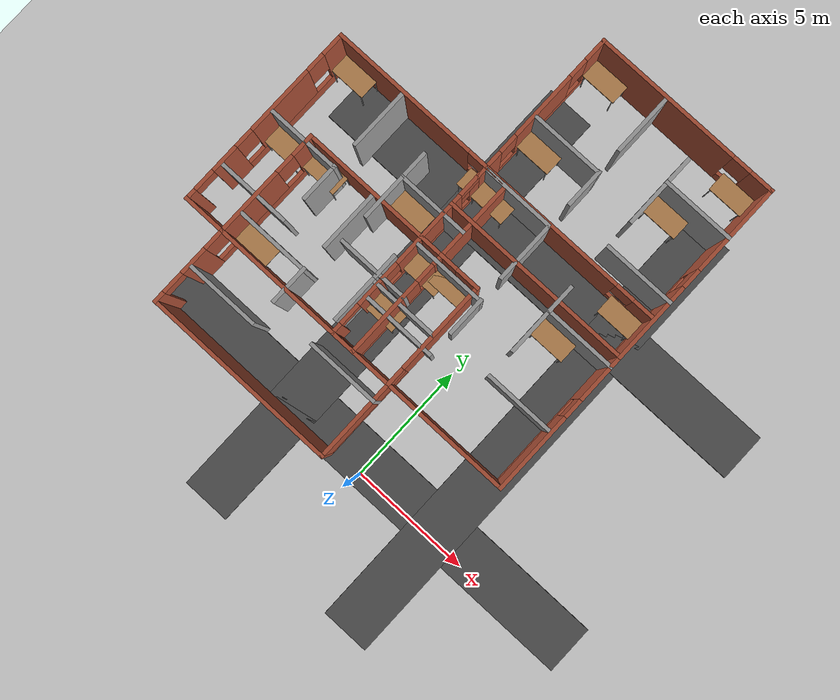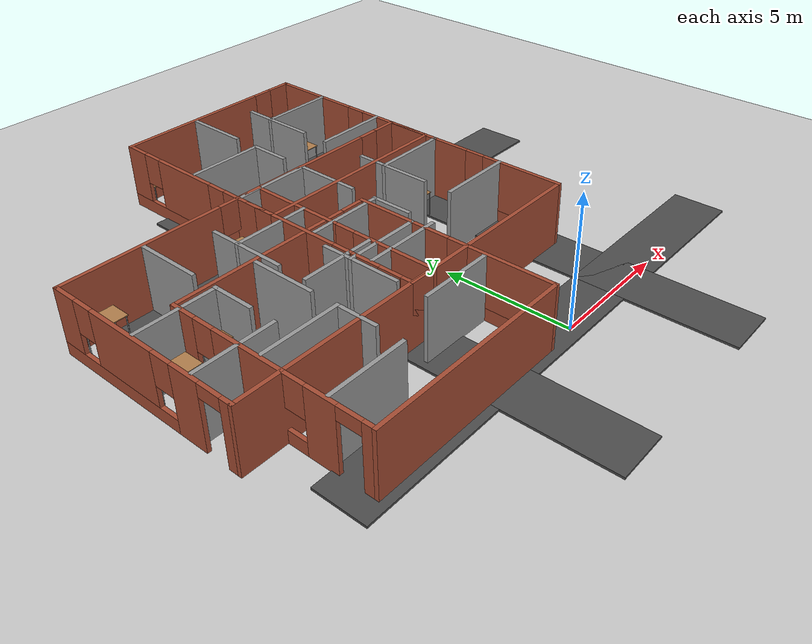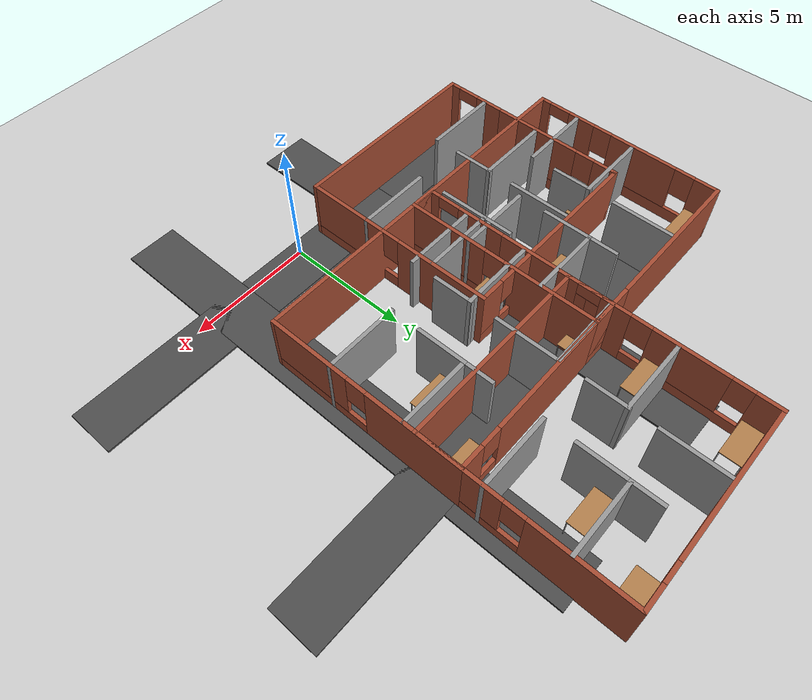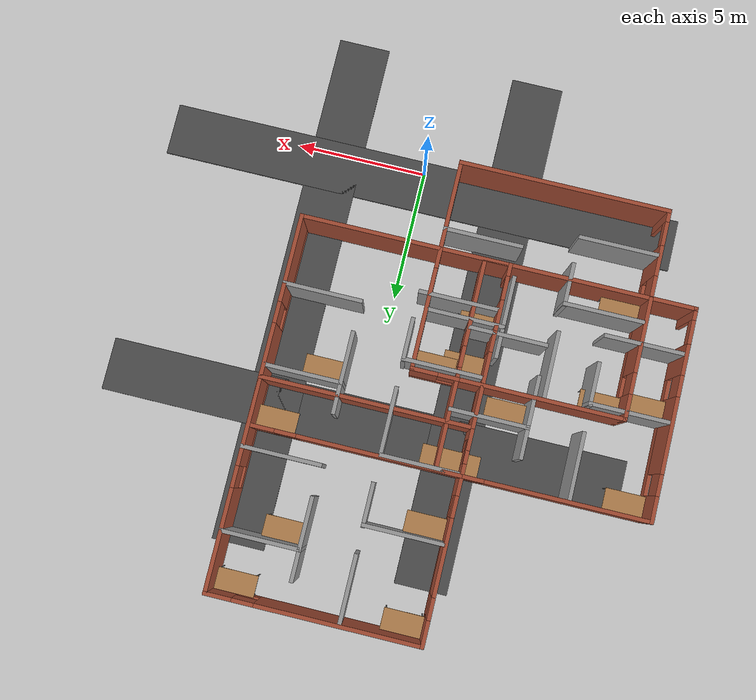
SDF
<sdf version="1.4">
 <world name="trial_1_world">
  <include><uri>model://ground_plane</uri></include>
  <plugin name="ros_interface_plugin" filename="librotors_gazebo_ros_interface_plugin.so"/>
  <include><uri>model://sun</uri></include>
  <include><uri>model://asphalt_road</uri><name>road1</name><pose>0 0.5 0 0 -0 1.57</pose></include>
  <include><uri>model://asphalt_road</uri><name>road2</name><pose>3.5 5.43 0 0 -0 0</pose></include>
  <include><uri>model://asphalt_road</uri><name>road3</name><pose>0 10 0 0 -0 1.57</pose></include>
  <include><uri>model://asphalt_road</uri><name>road4</name><pose>-3.5 5.43 0 0 -0 0</pose></include>
  <include><uri>model://office_2</uri><name>building4</name><pose>0 7.14 0.0 0 0 0</pose></include>
  <include><uri>model://office_2</uri><name>building23</name><pose>-6.90 7.14 0.0 0 0 0</pose></include>
  <include><uri>model://office_2</uri><name>building25</name><pose>-5.23 3.808 0.0 0 0 0</pose></include>
  <include><uri>model://office_2</uri><name>building32</name><pose>0 13.22 0.0 0 0 0</pose></include>
 </world>
</sdf>

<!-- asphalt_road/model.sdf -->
<sdf version='1.6'>
  <model name='asphalt_road'>
    <link name='link'>
      <self_collide>0</self_collide>
      <enable_wind>0</enable_wind>
      <kinematic>0</kinematic>
      <pose frame=''>0 0 0 0 0 0</pose>
      <gravity>1</gravity>
      <inertial>
        <mass>1</mass>
        <pose frame=''>0 0 0 0 -0 0</pose>
        <inertia>
          <ixx>1</ixx>
          <ixy>0</ixy>
          <ixz>0</ixz>
          <iyy>1</iyy>
          <iyz>0</iyz>
          <izz>1</izz>
        </inertia>
      </inertial>
      <visual name='visual'>
        <cast_shadows>0</cast_shadows>
        <geometry>
          <box>
            <size>2 20 0.1</size>
          </box>
        </geometry>
        <material>
          <script>
            <uri>model://asphalt_road/materials/scripts</uri>
            <uri>model://asphalt_road/materials/textures</uri>
            <name>vrc/asphalt_road</name>
          </script>
          <shader type='vertex'>
            <normal_map>__default__</normal_map>
          </shader>
          <ambient>0.5 0.5 0.5 1</ambient>
          <diffuse>0.5 0.5 0.5 1</diffuse>
          <specular>0.2 0.2 0.2 1</specular>
          <emissive>0 0 0 1</emissive>
        </material>
        <pose frame=''>0 0 0 0 -0 0</pose>
        <transparency>0</transparency>
      </visual>
      <collision name='collision'>
        <laser_retro>0</laser_retro>
        <max_contacts>10</max_contacts>
        <pose frame=''>0 0 0 0 -0 0</pose>
        <geometry>
          <box>
            <size>2 20 0.1</size>
          </box>
        </geometry>
        <surface>
          <friction>
            <ode>
              <mu>1</mu>
              <mu2>1</mu2>
              <fdir1>0 0 0</fdir1>
              <slip1>0</slip1>
              <slip2>0</slip2>
            </ode>
            <torsional>
              <coefficient>1</coefficient>
              <patch_radius>0</patch_radius>
              <surface_radius>0</surface_radius>
              <use_patch_radius>1</use_patch_radius>
              <ode>
                <slip>0</slip>
              </ode>
            </torsional>
          </friction>
          <bounce>
            <restitution_coefficient>0</restitution_coefficient>
            <threshold>1e+06</threshold>
          </bounce>
          <contact>
            <collide_without_contact>0</collide_without_contact>
            <collide_without_contact_bitmask>1</collide_without_contact_bitmask>
            <collide_bitmask>1</collide_bitmask>
            <ode>
              <soft_cfm>0</soft_cfm>
              <soft_erp>0.2</soft_erp>
              <kp>1e+13</kp>
              <kd>1</kd>
              <max_vel>0.01</max_vel>
              <min_depth>0</min_depth>
            </ode>
            <bullet>
              <split_impulse>1</split_impulse>
              <split_impulse_penetration_threshold>-0.01</split_impulse_penetration_threshold>
              <soft_cfm>0</soft_cfm>
              <soft_erp>0.2</soft_erp>
              <kp>1e+13</kp>
              <kd>1</kd>
            </bullet>
          </contact>
        </surface>
      </collision>
    </link>
    <static>1</static>
    <allow_auto_disable>1</allow_auto_disable>
  </model>
</sdf>

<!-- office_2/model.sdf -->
<sdf version='1.7'>
  <model name='office'>
    <link name='Wall_1'>
      <pose>-0.000184 -3.925 0 0 -0 0</pose>
      <self_collide>0</self_collide>
      <enable_wind>0</enable_wind>
      <kinematic>0</kinematic>
      <visual name='Wall_1_Visual'>
        <pose>0 0 1.25 0 -0 0</pose>
        <geometry>
          <box>
            <size>8 0.15 2.5</size>
          </box>
        </geometry>
        <material>
          <script>
            <uri>file://media/materials/scripts/gazebo.material</uri>
            <name>Gazebo/Bricks</name>
          </script>
          <ambient>1 1 1 1</ambient>
          <shader type='pixel'/>
        </material>
        <meta>
          <layer>0</layer>
        </meta>
        <transparency>0</transparency>
        <cast_shadows>1</cast_shadows>
      </visual>
      <collision name='Wall_1_Collision'>
        <laser_retro>0</laser_retro>
        <max_contacts>10</max_contacts>
        <pose>0 0 1.25 0 -0 0</pose>
        <geometry>
          <box>
            <size>8 0.15 2.5</size>
          </box>
        </geometry>
        <surface>
          <friction>
            <ode>
              <mu>1</mu>
              <mu2>1</mu2>
              <fdir1>0 0 0</fdir1>
              <slip1>0</slip1>
              <slip2>0</slip2>
            </ode>
            <torsional>
              <coefficient>1</coefficient>
              <patch_radius>0</patch_radius>
              <surface_radius>0</surface_radius>
              <use_patch_radius>1</use_patch_radius>
              <ode>
                <slip>0</slip>
              </ode>
            </torsional>
          </friction>
          <bounce>
            <restitution_coefficient>0</restitution_coefficient>
            <threshold>1e+06</threshold>
          </bounce>
          <contact>
            <collide_without_contact>0</collide_without_contact>
            <collide_without_contact_bitmask>1</collide_without_contact_bitmask>
            <collide_bitmask>1</collide_bitmask>
            <ode>
              <soft_cfm>0</soft_cfm>
              <soft_erp>0.2</soft_erp>
              <kp>1e+13</kp>
              <kd>1</kd>
              <max_vel>0.01</max_vel>
              <min_depth>0</min_depth>
            </ode>
            <bullet>
              <split_impulse>1</split_impulse>
              <split_impulse_penetration_threshold>-0.01</split_impulse_penetration_threshold>
              <soft_cfm>0</soft_cfm>
              <soft_erp>0.2</soft_erp>
              <kp>1e+13</kp>
              <kd>1</kd>
            </bullet>
          </contact>
        </surface>
      </collision>
    </link>
    <link name='Wall_12'>
      <pose>2.49174 1.69053 0 0 -0 3.14159</pose>
      <self_collide>0</self_collide>
      <enable_wind>0</enable_wind>
      <kinematic>0</kinematic>
      <visual name='Wall_12_Visual'>
        <pose>0 0 1.25 0 -0 0</pose>
        <geometry>
          <box>
            <size>3 0.15 2.5</size>
          </box>
        </geometry>
        <material>
          <script>
            <uri>file://media/materials/scripts/gazebo.material</uri>
            <name>Gazebo/Grey</name>
          </script>
          <ambient>1 1 1 1</ambient>
          <shader type='pixel'/>
        </material>
        <meta>
          <layer>0</layer>
        </meta>
        <transparency>0</transparency>
        <cast_shadows>1</cast_shadows>
      </visual>
      <collision name='Wall_12_Collision'>
        <laser_retro>0</laser_retro>
        <max_contacts>10</max_contacts>
        <pose>0 0 1.25 0 -0 0</pose>
        <geometry>
          <box>
            <size>3 0.15 2.5</size>
          </box>
        </geometry>
        <surface>
          <friction>
            <ode>
              <mu>1</mu>
              <mu2>1</mu2>
              <fdir1>0 0 0</fdir1>
              <slip1>0</slip1>
              <slip2>0</slip2>
            </ode>
            <torsional>
              <coefficient>1</coefficient>
              <patch_radius>0</patch_radius>
              <surface_radius>0</surface_radius>
              <use_patch_radius>1</use_patch_radius>
              <ode>
                <slip>0</slip>
              </ode>
            </torsional>
          </friction>
          <bounce>
            <restitution_coefficient>0</restitution_coefficient>
            <threshold>1e+06</threshold>
          </bounce>
          <contact>
            <collide_without_contact>0</collide_without_contact>
            <collide_without_contact_bitmask>1</collide_without_contact_bitmask>
            <collide_bitmask>1</collide_bitmask>
            <ode>
              <soft_cfm>0</soft_cfm>
              <soft_erp>0.2</soft_erp>
              <kp>1e+13</kp>
              <kd>1</kd>
              <max_vel>0.01</max_vel>
              <min_depth>0</min_depth>
            </ode>
            <bullet>
              <split_impulse>1</split_impulse>
              <split_impulse_penetration_threshold>-0.01</split_impulse_penetration_threshold>
              <soft_cfm>0</soft_cfm>
              <soft_erp>0.2</soft_erp>
              <kp>1e+13</kp>
              <kd>1</kd>
            </bullet>
          </contact>
        </surface>
      </collision>
    </link>
    <link name='Wall_13'>
      <pose>1.06675 2.24053 0 0 -0 1.5708</pose>
      <self_collide>0</self_collide>
      <enable_wind>0</enable_wind>
      <kinematic>0</kinematic>
      <visual name='Wall_13_Visual'>
        <pose>0 0 1.25 0 -0 0</pose>
        <geometry>
          <box>
            <size>1.25 0.15 2.5</size>
          </box>
        </geometry>
        <material>
          <script>
            <uri>file://media/materials/scripts/gazebo.material</uri>
            <name>Gazebo/Grey</name>
          </script>
          <ambient>1 1 1 1</ambient>
          <shader type='pixel'/>
        </material>
        <meta>
          <layer>0</layer>
        </meta>
        <transparency>0</transparency>
        <cast_shadows>1</cast_shadows>
      </visual>
      <collision name='Wall_13_Collision'>
        <laser_retro>0</laser_retro>
        <max_contacts>10</max_contacts>
        <pose>0 0 1.25 0 -0 0</pose>
        <geometry>
          <box>
            <size>1.25 0.15 2.5</size>
          </box>
        </geometry>
        <surface>
          <friction>
            <ode>
              <mu>1</mu>
              <mu2>1</mu2>
              <fdir1>0 0 0</fdir1>
              <slip1>0</slip1>
              <slip2>0</slip2>
            </ode>
            <torsional>
              <coefficient>1</coefficient>
              <patch_radius>0</patch_radius>
              <surface_radius>0</surface_radius>
              <use_patch_radius>1</use_patch_radius>
              <ode>
                <slip>0</slip>
              </ode>
            </torsional>
          </friction>
          <bounce>
            <restitution_coefficient>0</restitution_coefficient>
            <threshold>1e+06</threshold>
          </bounce>
          <contact>
            <collide_without_contact>0</collide_without_contact>
            <collide_without_contact_bitmask>1</collide_without_contact_bitmask>
            <collide_bitmask>1</collide_bitmask>
            <ode>
              <soft_cfm>0</soft_cfm>
              <soft_erp>0.2</soft_erp>
              <kp>1e+13</kp>
              <kd>1</kd>
              <max_vel>0.01</max_vel>
              <min_depth>0</min_depth>
            </ode>
            <bullet>
              <split_impulse>1</split_impulse>
              <split_impulse_penetration_threshold>-0.01</split_impulse_penetration_threshold>
              <soft_cfm>0</soft_cfm>
              <soft_erp>0.2</soft_erp>
              <kp>1e+13</kp>
              <kd>1</kd>
            </bullet>
          </contact>
        </surface>
      </collision>
    </link>
    <link name='Wall_17'>
      <pose>-2.36974 0.32839 0 0 -0 0</pose>
      <self_collide>0</self_collide>
      <enable_wind>0</enable_wind>
      <kinematic>0</kinematic>
      <visual name='Wall_17_Visual'>
        <pose>0 0 1.25 0 -0 0</pose>
        <geometry>
          <box>
            <size>3.04046 0.15 2.5</size>
          </box>
        </geometry>
        <material>
          <script>
            <uri>file://media/materials/scripts/gazebo.material</uri>
            <name>Gazebo/Grey</name>
          </script>
          <ambient>1 1 1 1</ambient>
          <shader type='pixel'/>
        </material>
        <meta>
          <layer>0</layer>
        </meta>
        <transparency>0</transparency>
        <cast_shadows>1</cast_shadows>
      </visual>
      <collision name='Wall_17_Collision'>
        <laser_retro>0</laser_retro>
        <max_contacts>10</max_contacts>
        <pose>0 0 1.25 0 -0 0</pose>
        <geometry>
          <box>
            <size>3.04046 0.15 2.5</size>
          </box>
        </geometry>
        <surface>
          <friction>
            <ode>
              <mu>1</mu>
              <mu2>1</mu2>
              <fdir1>0 0 0</fdir1>
              <slip1>0</slip1>
              <slip2>0</slip2>
            </ode>
            <torsional>
              <coefficient>1</coefficient>
              <patch_radius>0</patch_radius>
              <surface_radius>0</surface_radius>
              <use_patch_radius>1</use_patch_radius>
              <ode>
                <slip>0</slip>
              </ode>
            </torsional>
          </friction>
          <bounce>
            <restitution_coefficient>0</restitution_coefficient>
            <threshold>1e+06</threshold>
          </bounce>
          <contact>
            <collide_without_contact>0</collide_without_contact>
            <collide_without_contact_bitmask>1</collide_without_contact_bitmask>
            <collide_bitmask>1</collide_bitmask>
            <ode>
              <soft_cfm>0</soft_cfm>
              <soft_erp>0.2</soft_erp>
              <kp>1e+13</kp>
              <kd>1</kd>
              <max_vel>0.01</max_vel>
              <min_depth>0</min_depth>
            </ode>
            <bullet>
              <split_impulse>1</split_impulse>
              <split_impulse_penetration_threshold>-0.01</split_impulse_penetration_threshold>
              <soft_cfm>0</soft_cfm>
              <soft_erp>0.2</soft_erp>
              <kp>1e+13</kp>
              <kd>1</kd>
            </bullet>
          </contact>
        </surface>
      </collision>
    </link>
    <link name='Wall_20'>
      <pose>-0.929909 2.60455 0 0 0 -1.5708</pose>
      <self_collide>0</self_collide>
      <enable_wind>0</enable_wind>
      <kinematic>0</kinematic>
      <visual name='Wall_20_Visual'>
        <pose>0 0 1.25 0 -0 0</pose>
        <geometry>
          <box>
            <size>2.5 0.15 2.5</size>
          </box>
        </geometry>
        <material>
          <script>
            <uri>file://media/materials/scripts/gazebo.material</uri>
            <name>Gazebo/Grey</name>
          </script>
          <ambient>1 1 1 1</ambient>
          <shader type='pixel'/>
        </material>
        <meta>
          <layer>0</layer>
        </meta>
        <transparency>0</transparency>
        <cast_shadows>1</cast_shadows>
      </visual>
      <collision name='Wall_20_Collision'>
        <laser_retro>0</laser_retro>
        <max_contacts>10</max_contacts>
        <pose>0 0 1.25 0 -0 0</pose>
        <geometry>
          <box>
            <size>2.5 0.15 2.5</size>
          </box>
        </geometry>
        <surface>
          <friction>
            <ode>
              <mu>1</mu>
              <mu2>1</mu2>
              <fdir1>0 0 0</fdir1>
              <slip1>0</slip1>
              <slip2>0</slip2>
            </ode>
            <torsional>
              <coefficient>1</coefficient>
              <patch_radius>0</patch_radius>
              <surface_radius>0</surface_radius>
              <use_patch_radius>1</use_patch_radius>
              <ode>
                <slip>0</slip>
              </ode>
            </torsional>
          </friction>
          <bounce>
            <restitution_coefficient>0</restitution_coefficient>
            <threshold>1e+06</threshold>
          </bounce>
          <contact>
            <collide_without_contact>0</collide_without_contact>
            <collide_without_contact_bitmask>1</collide_without_contact_bitmask>
            <collide_bitmask>1</collide_bitmask>
            <ode>
              <soft_cfm>0</soft_cfm>
              <soft_erp>0.2</soft_erp>
              <kp>1e+13</kp>
              <kd>1</kd>
              <max_vel>0.01</max_vel>
              <min_depth>0</min_depth>
            </ode>
            <bullet>
              <split_impulse>1</split_impulse>
              <split_impulse_penetration_threshold>-0.01</split_impulse_penetration_threshold>
              <soft_cfm>0</soft_cfm>
              <soft_erp>0.2</soft_erp>
              <kp>1e+13</kp>
              <kd>1</kd>
            </bullet>
          </contact>
        </surface>
      </collision>
    </link>
    <link name='Wall_31'>
      <pose>-2.38551 -2.21028 0 0 -0 0</pose>
      <self_collide>0</self_collide>
      <enable_wind>0</enable_wind>
      <kinematic>0</kinematic>
      <visual name='Wall_31_Visual'>
        <pose>0 0 1.25 0 -0 0</pose>
        <geometry>
          <box>
            <size>3 0.15 2.5</size>
          </box>
        </geometry>
        <material>
          <script>
            <uri>file://media/materials/scripts/gazebo.material</uri>
            <name>Gazebo/Grey</name>
          </script>
          <ambient>1 1 1 1</ambient>
          <shader type='pixel'/>
        </material>
        <meta>
          <layer>0</layer>
        </meta>
        <transparency>0</transparency>
        <cast_shadows>1</cast_shadows>
      </visual>
      <collision name='Wall_31_Collision'>
        <laser_retro>0</laser_retro>
        <max_contacts>10</max_contacts>
        <pose>0 0 1.25 0 -0 0</pose>
        <geometry>
          <box>
            <size>3 0.15 2.5</size>
          </box>
        </geometry>
        <surface>
          <friction>
            <ode>
              <mu>1</mu>
              <mu2>1</mu2>
              <fdir1>0 0 0</fdir1>
              <slip1>0</slip1>
              <slip2>0</slip2>
            </ode>
            <torsional>
              <coefficient>1</coefficient>
              <patch_radius>0</patch_radius>
              <surface_radius>0</surface_radius>
              <use_patch_radius>1</use_patch_radius>
              <ode>
                <slip>0</slip>
              </ode>
            </torsional>
          </friction>
          <bounce>
            <restitution_coefficient>0</restitution_coefficient>
            <threshold>1e+06</threshold>
          </bounce>
          <contact>
            <collide_without_contact>0</collide_without_contact>
            <collide_without_contact_bitmask>1</collide_without_contact_bitmask>
            <collide_bitmask>1</collide_bitmask>
            <ode>
              <soft_cfm>0</soft_cfm>
              <soft_erp>0.2</soft_erp>
              <kp>1e+13</kp>
              <kd>1</kd>
              <max_vel>0.01</max_vel>
              <min_depth>0</min_depth>
            </ode>
            <bullet>
              <split_impulse>1</split_impulse>
              <split_impulse_penetration_threshold>-0.01</split_impulse_penetration_threshold>
              <soft_cfm>0</soft_cfm>
              <soft_erp>0.2</soft_erp>
              <kp>1e+13</kp>
              <kd>1</kd>
            </bullet>
          </contact>
        </surface>
      </collision>
    </link>
    <link name='Wall_33'>
      <pose>-0.924514 -0.397442 0 0 -0 1.5708</pose>
      <self_collide>0</self_collide>
      <enable_wind>0</enable_wind>
      <kinematic>0</kinematic>
      <visual name='Wall_33_Visual'>
        <pose>0 0 1.25 0 -0 0</pose>
        <geometry>
          <box>
            <size>1.6556 0.15 2.5</size>
          </box>
        </geometry>
        <material>
          <script>
            <uri>file://media/materials/scripts/gazebo.material</uri>
            <name>Gazebo/Grey</name>
          </script>
          <ambient>1 1 1 1</ambient>
          <shader type='pixel'/>
        </material>
        <meta>
          <layer>0</layer>
        </meta>
        <transparency>0</transparency>
        <cast_shadows>1</cast_shadows>
      </visual>
      <collision name='Wall_33_Collision'>
        <laser_retro>0</laser_retro>
        <max_contacts>10</max_contacts>
        <pose>0 0 1.25 0 -0 0</pose>
        <geometry>
          <box>
            <size>1.6556 0.15 2.5</size>
          </box>
        </geometry>
        <surface>
          <friction>
            <ode>
              <mu>1</mu>
              <mu2>1</mu2>
              <fdir1>0 0 0</fdir1>
              <slip1>0</slip1>
              <slip2>0</slip2>
            </ode>
            <torsional>
              <coefficient>1</coefficient>
              <patch_radius>0</patch_radius>
              <surface_radius>0</surface_radius>
              <use_patch_radius>1</use_patch_radius>
              <ode>
                <slip>0</slip>
              </ode>
            </torsional>
          </friction>
          <bounce>
            <restitution_coefficient>0</restitution_coefficient>
            <threshold>1e+06</threshold>
          </bounce>
          <contact>
            <collide_without_contact>0</collide_without_contact>
            <collide_without_contact_bitmask>1</collide_without_contact_bitmask>
            <collide_bitmask>1</collide_bitmask>
            <ode>
              <soft_cfm>0</soft_cfm>
              <soft_erp>0.2</soft_erp>
              <kp>1e+13</kp>
              <kd>1</kd>
              <max_vel>0.01</max_vel>
              <min_depth>0</min_depth>
            </ode>
            <bullet>
              <split_impulse>1</split_impulse>
              <split_impulse_penetration_threshold>-0.01</split_impulse_penetration_threshold>
              <soft_cfm>0</soft_cfm>
              <soft_erp>0.2</soft_erp>
              <kp>1e+13</kp>
              <kd>1</kd>
            </bullet>
          </contact>
        </surface>
      </collision>
    </link>
    <link name='Wall_38'>
      <pose>2.50019 -1.35896 0 0 -0 0</pose>
      <self_collide>0</self_collide>
      <enable_wind>0</enable_wind>
      <kinematic>0</kinematic>
      <visual name='Wall_38_Visual'>
        <pose>0 0 1.25 0 -0 0</pose>
        <geometry>
          <box>
            <size>3 0.15 2.5</size>
          </box>
        </geometry>
        <material>
          <script>
            <uri>file://media/materials/scripts/gazebo.material</uri>
            <name>Gazebo/Grey</name>
          </script>
          <ambient>1 1 1 1</ambient>
          <shader type='pixel'/>
        </material>
        <meta>
          <layer>0</layer>
        </meta>
        <transparency>0</transparency>
        <cast_shadows>1</cast_shadows>
      </visual>
      <collision name='Wall_38_Collision'>
        <laser_retro>0</laser_retro>
        <max_contacts>10</max_contacts>
        <pose>0 0 1.25 0 -0 0</pose>
        <geometry>
          <box>
            <size>3 0.15 2.5</size>
          </box>
        </geometry>
        <surface>
          <friction>
            <ode>
              <mu>1</mu>
              <mu2>1</mu2>
              <fdir1>0 0 0</fdir1>
              <slip1>0</slip1>
              <slip2>0</slip2>
            </ode>
            <torsional>
              <coefficient>1</coefficient>
              <patch_radius>0</patch_radius>
              <surface_radius>0</surface_radius>
              <use_patch_radius>1</use_patch_radius>
              <ode>
                <slip>0</slip>
              </ode>
            </torsional>
          </friction>
          <bounce>
            <restitution_coefficient>0</restitution_coefficient>
            <threshold>1e+06</threshold>
          </bounce>
          <contact>
            <collide_without_contact>0</collide_without_contact>
            <collide_without_contact_bitmask>1</collide_without_contact_bitmask>
            <collide_bitmask>1</collide_bitmask>
            <ode>
              <soft_cfm>0</soft_cfm>
              <soft_erp>0.2</soft_erp>
              <kp>1e+13</kp>
              <kd>1</kd>
              <max_vel>0.01</max_vel>
              <min_depth>0</min_depth>
            </ode>
            <bullet>
              <split_impulse>1</split_impulse>
              <split_impulse_penetration_threshold>-0.01</split_impulse_penetration_threshold>
              <soft_cfm>0</soft_cfm>
              <soft_erp>0.2</soft_erp>
              <kp>1e+13</kp>
              <kd>1</kd>
            </bullet>
          </contact>
        </surface>
      </collision>
    </link>
    <link name='Wall_4'>
      <pose>-3.92518 0 0 0 -0 1.5708</pose>
      <self_collide>0</self_collide>
      <enable_wind>0</enable_wind>
      <kinematic>0</kinematic>
      <visual name='Wall_4_Visual_0'>
        <pose>-3.75034 0 1.25 0 -0 0</pose>
        <geometry>
          <box>
            <size>0.499317 0.15 2.5</size>
          </box>
        </geometry>
        <material>
          <script>
            <uri>file://media/materials/scripts/gazebo.material</uri>
            <name>Gazebo/Bricks</name>
          </script>
          <ambient>1 1 1 1</ambient>
          <shader type='pixel'/>
        </material>
        <meta>
          <layer>0</layer>
        </meta>
        <transparency>0</transparency>
        <cast_shadows>1</cast_shadows>
      </visual>
      <visual name='Wall_4_Visual_1'>
        <pose>-2.02188 0 1.25 0 -0 0</pose>
        <geometry>
          <box>
            <size>1.15762 0.15 2.5</size>
          </box>
        </geometry>
        <material>
          <script>
            <uri>file://media/materials/scripts/gazebo.material</uri>
            <name>Gazebo/Bricks</name>
          </script>
          <ambient>1 1 1 1</ambient>
          <shader type='pixel'/>
        </material>
        <meta>
          <layer>0</layer>
        </meta>
        <transparency>0</transparency>
        <cast_shadows>1</cast_shadows>
      </visual>
      <visual name='Wall_4_Visual_2'>
        <pose>1.27847 0 0.25 0 -0 0</pose>
        <geometry>
          <box>
            <size>5.44307 0.15 0.5</size>
          </box>
        </geometry>
        <material>
          <script>
            <uri>file://media/materials/scripts/gazebo.material</uri>
            <name>Gazebo/Bricks</name>
          </script>
          <ambient>1 1 1 1</ambient>
          <shader type='pixel'/>
        </material>
        <meta>
          <layer>0</layer>
        </meta>
        <transparency>0</transparency>
        <cast_shadows>1</cast_shadows>
      </visual>
      <visual name='Wall_4_Visual_3'>
        <pose>0.775576 0 1.5 0 -0 0</pose>
        <geometry>
          <box>
            <size>2.83728 0.15 2</size>
          </box>
        </geometry>
        <material>
          <script>
            <uri>file://media/materials/scripts/gazebo.material</uri>
            <name>Gazebo/Bricks</name>
          </script>
          <ambient>1 1 1 1</ambient>
          <shader type='pixel'/>
        </material>
        <meta>
          <layer>0</layer>
        </meta>
        <transparency>0</transparency>
        <cast_shadows>1</cast_shadows>
      </visual>
      <visual name='Wall_4_Visual_4'>
        <pose>3.49711 0 1.5 0 -0 0</pose>
        <geometry>
          <box>
            <size>1.00578 0.15 2</size>
          </box>
        </geometry>
        <material>
          <script>
            <uri>file://media/materials/scripts/gazebo.material</uri>
            <name>Gazebo/Bricks</name>
          </script>
          <ambient>1 1 1 1</ambient>
          <shader type='pixel'/>
        </material>
        <meta>
          <layer>0</layer>
        </meta>
        <transparency>0</transparency>
        <cast_shadows>1</cast_shadows>
      </visual>
      <visual name='Wall_4_Visual_5'>
        <pose>-1.04307 0 1.9 0 -0 0</pose>
        <geometry>
          <box>
            <size>0.8 0.15 1.2</size>
          </box>
        </geometry>
        <material>
          <script>
            <uri>file://media/materials/scripts/gazebo.material</uri>
            <name>Gazebo/Bricks</name>
          </script>
          <ambient>1 1 1 1</ambient>
          <shader type='pixel'/>
        </material>
        <meta>
          <layer>0</layer>
        </meta>
        <transparency>0</transparency>
        <cast_shadows>1</cast_shadows>
      </visual>
      <visual name='Wall_4_Visual_6'>
        <pose>2.59422 0 1.9 0 -0 0</pose>
        <geometry>
          <box>
            <size>0.8 0.15 1.2</size>
          </box>
        </geometry>
        <material>
          <script>
            <uri>file://media/materials/scripts/gazebo.material</uri>
            <name>Gazebo/Bricks</name>
          </script>
          <ambient>1 1 1 1</ambient>
          <shader type='pixel'/>
        </material>
        <meta>
          <layer>0</layer>
        </meta>
        <transparency>0</transparency>
        <cast_shadows>1</cast_shadows>
      </visual>
      <visual name='Wall_4_Visual_7'>
        <pose>-3.05068 0 2.25 0 -0 0</pose>
        <geometry>
          <box>
            <size>0.9 0.15 0.5</size>
          </box>
        </geometry>
        <material>
          <script>
            <uri>file://media/materials/scripts/gazebo.material</uri>
            <name>Gazebo/Bricks</name>
          </script>
          <ambient>1 1 1 1</ambient>
          <shader type='pixel'/>
        </material>
        <meta>
          <layer>0</layer>
        </meta>
        <transparency>0</transparency>
        <cast_shadows>1</cast_shadows>
      </visual>
      <collision name='Wall_4_Collision_0'>
        <laser_retro>0</laser_retro>
        <max_contacts>10</max_contacts>
        <pose>-3.75034 0 1.25 0 -0 0</pose>
        <geometry>
          <box>
            <size>0.499317 0.15 2.5</size>
          </box>
        </geometry>
        <surface>
          <friction>
            <ode>
              <mu>1</mu>
              <mu2>1</mu2>
              <fdir1>0 0 0</fdir1>
              <slip1>0</slip1>
              <slip2>0</slip2>
            </ode>
            <torsional>
              <coefficient>1</coefficient>
              <patch_radius>0</patch_radius>
              <surface_radius>0</surface_radius>
              <use_patch_radius>1</use_patch_radius>
              <ode>
                <slip>0</slip>
              </ode>
            </torsional>
          </friction>
          <bounce>
            <restitution_coefficient>0</restitution_coefficient>
            <threshold>1e+06</threshold>
          </bounce>
          <contact>
            <collide_without_contact>0</collide_without_contact>
            <collide_without_contact_bitmask>1</collide_without_contact_bitmask>
            <collide_bitmask>1</collide_bitmask>
            <ode>
              <soft_cfm>0</soft_cfm>
              <soft_erp>0.2</soft_erp>
              <kp>1e+13</kp>
              <kd>1</kd>
              <max_vel>0.01</max_vel>
              <min_depth>0</min_depth>
            </ode>
            <bullet>
              <split_impulse>1</split_impulse>
              <split_impulse_penetration_threshold>-0.01</split_impulse_penetration_threshold>
              <soft_cfm>0</soft_cfm>
              <soft_erp>0.2</soft_erp>
              <kp>1e+13</kp>
              <kd>1</kd>
            </bullet>
          </contact>
        </surface>
      </collision>
      <collision name='Wall_4_Collision_1'>
        <laser_retro>0</laser_retro>
        <max_contacts>10</max_contacts>
        <pose>-2.02188 0 1.25 0 -0 0</pose>
        <geometry>
          <box>
            <size>1.15762 0.15 2.5</size>
          </box>
        </geometry>
        <surface>
          <friction>
            <ode>
              <mu>1</mu>
              <mu2>1</mu2>
              <fdir1>0 0 0</fdir1>
              <slip1>0</slip1>
              <slip2>0</slip2>
            </ode>
            <torsional>
              <coefficient>1</coefficient>
              <patch_radius>0</patch_radius>
              <surface_radius>0</surface_radius>
              <use_patch_radius>1</use_patch_radius>
              <ode>
                <slip>0</slip>
              </ode>
            </torsional>
          </friction>
          <bounce>
            <restitution_coefficient>0</restitution_coefficient>
            <threshold>1e+06</threshold>
          </bounce>
          <contact>
            <collide_without_contact>0</collide_without_contact>
            <collide_without_contact_bitmask>1</collide_without_contact_bitmask>
            <collide_bitmask>1</collide_bitmask>
            <ode>
              <soft_cfm>0</soft_cfm>
              <soft_erp>0.2</soft_erp>
              <kp>1e+13</kp>
              <kd>1</kd>
              <max_vel>0.01</max_vel>
              <min_depth>0</min_depth>
            </ode>
            <bullet>
              <split_impulse>1</split_impulse>
              <split_impulse_penetration_threshold>-0.01</split_impulse_penetration_threshold>
              <soft_cfm>0</soft_cfm>
              <soft_erp>0.2</soft_erp>
              <kp>1e+13</kp>
              <kd>1</kd>
            </bullet>
          </contact>
        </surface>
      </collision>
      <collision name='Wall_4_Collision_2'>
        <laser_retro>0</laser_retro>
        <max_contacts>10</max_contacts>
        <pose>1.27847 0 0.25 0 -0 0</pose>
        <geometry>
          <box>
            <size>5.44307 0.15 0.5</size>
          </box>
        </geometry>
        <surface>
          <friction>
            <ode>
              <mu>1</mu>
              <mu2>1</mu2>
              <fdir1>0 0 0</fdir1>
              <slip1>0</slip1>
              <slip2>0</slip2>
            </ode>
            <torsional>
              <coefficient>1</coefficient>
              <patch_radius>0</patch_radius>
              <surface_radius>0</surface_radius>
              <use_patch_radius>1</use_patch_radius>
              <ode>
                <slip>0</slip>
              </ode>
            </torsional>
          </friction>
          <bounce>
            <restitution_coefficient>0</restitution_coefficient>
            <threshold>1e+06</threshold>
          </bounce>
          <contact>
            <collide_without_contact>0</collide_without_contact>
            <collide_without_contact_bitmask>1</collide_without_contact_bitmask>
            <collide_bitmask>1</collide_bitmask>
            <ode>
              <soft_cfm>0</soft_cfm>
              <soft_erp>0.2</soft_erp>
              <kp>1e+13</kp>
              <kd>1</kd>
              <max_vel>0.01</max_vel>
              <min_depth>0</min_depth>
            </ode>
            <bullet>
              <split_impulse>1</split_impulse>
              <split_impulse_penetration_threshold>-0.01</split_impulse_penetration_threshold>
              <soft_cfm>0</soft_cfm>
              <soft_erp>0.2</soft_erp>
              <kp>1e+13</kp>
              <kd>1</kd>
            </bullet>
          </contact>
        </surface>
      </collision>
      <collision name='Wall_4_Collision_3'>
        <laser_retro>0</laser_retro>
        <max_contacts>10</max_contacts>
        <pose>0.775576 0 1.5 0 -0 0</pose>
        <geometry>
          <box>
            <size>2.83728 0.15 2</size>
          </box>
        </geometry>
        <surface>
          <friction>
            <ode>
              <mu>1</mu>
              <mu2>1</mu2>
              <fdir1>0 0 0</fdir1>
              <slip1>0</slip1>
              <slip2>0</slip2>
            </ode>
            <torsional>
              <coefficient>1</coefficient>
              <patch_radius>0</patch_radius>
              <surface_radius>0</surface_radius>
              <use_patch_radius>1</use_patch_radius>
              <ode>
                <slip>0</slip>
              </ode>
            </torsional>
          </friction>
          <bounce>
            <restitution_coefficient>0</restitution_coefficient>
            <threshold>1e+06</threshold>
          </bounce>
          <contact>
            <collide_without_contact>0</collide_without_contact>
            <collide_without_contact_bitmask>1</collide_without_contact_bitmask>
            <collide_bitmask>1</collide_bitmask>
            <ode>
              <soft_cfm>0</soft_cfm>
              <soft_erp>0.2</soft_erp>
              <kp>1e+13</kp>
              <kd>1</kd>
              <max_vel>0.01</max_vel>
              <min_depth>0</min_depth>
            </ode>
            <bullet>
              <split_impulse>1</split_impulse>
              <split_impulse_penetration_threshold>-0.01</split_impulse_penetration_threshold>
              <soft_cfm>0</soft_cfm>
              <soft_erp>0.2</soft_erp>
              <kp>1e+13</kp>
              <kd>1</kd>
            </bullet>
          </contact>
        </surface>
      </collision>
      <collision name='Wall_4_Collision_4'>
        <laser_retro>0</laser_retro>
        <max_contacts>10</max_contacts>
        <pose>3.49711 0 1.5 0 -0 0</pose>
        <geometry>
          <box>
            <size>1.00578 0.15 2</size>
          </box>
        </geometry>
        <surface>
          <friction>
            <ode>
              <mu>1</mu>
              <mu2>1</mu2>
              <fdir1>0 0 0</fdir1>
              <slip1>0</slip1>
              <slip2>0</slip2>
            </ode>
            <torsional>
              <coefficient>1</coefficient>
              <patch_radius>0</patch_radius>
              <surface_radius>0</surface_radius>
              <use_patch_radius>1</use_patch_radius>
              <ode>
                <slip>0</slip>
              </ode>
            </torsional>
          </friction>
          <bounce>
            <restitution_coefficient>0</restitution_coefficient>
            <threshold>1e+06</threshold>
          </bounce>
          <contact>
            <collide_without_contact>0</collide_without_contact>
            <collide_without_contact_bitmask>1</collide_without_contact_bitmask>
            <collide_bitmask>1</collide_bitmask>
            <ode>
              <soft_cfm>0</soft_cfm>
              <soft_erp>0.2</soft_erp>
              <kp>1e+13</kp>
              <kd>1</kd>
              <max_vel>0.01</max_vel>
              <min_depth>0</min_depth>
            </ode>
            <bullet>
              <split_impulse>1</split_impulse>
              <split_impulse_penetration_threshold>-0.01</split_impulse_penetration_threshold>
              <soft_cfm>0</soft_cfm>
              <soft_erp>0.2</soft_erp>
              <kp>1e+13</kp>
              <kd>1</kd>
            </bullet>
          </contact>
        </surface>
      </collision>
      <collision name='Wall_4_Collision_5'>
        <laser_retro>0</laser_retro>
        <max_contacts>10</max_contacts>
        <pose>-1.04307 0 1.9 0 -0 0</pose>
        <geometry>
          <box>
            <size>0.8 0.15 1.2</size>
          </box>
        </geometry>
        <surface>
          <friction>
            <ode>
              <mu>1</mu>
              <mu2>1</mu2>
              <fdir1>0 0 0</fdir1>
              <slip1>0</slip1>
              <slip2>0</slip2>
            </ode>
            <torsional>
              <coefficient>1</coefficient>
              <patch_radius>0</patch_radius>
              <surface_radius>0</surface_radius>
              <use_patch_radius>1</use_patch_radius>
              <ode>
                <slip>0</slip>
              </ode>
            </torsional>
          </friction>
          <bounce>
            <restitution_coefficient>0</restitution_coefficient>
            <threshold>1e+06</threshold>
          </bounce>
          <contact>
            <collide_without_contact>0</collide_without_contact>
            <collide_without_contact_bitmask>1</collide_without_contact_bitmask>
            <collide_bitmask>1</collide_bitmask>
            <ode>
              <soft_cfm>0</soft_cfm>
              <soft_erp>0.2</soft_erp>
              <kp>1e+13</kp>
              <kd>1</kd>
              <max_vel>0.01</max_vel>
              <min_depth>0</min_depth>
            </ode>
            <bullet>
              <split_impulse>1</split_impulse>
              <split_impulse_penetration_threshold>-0.01</split_impulse_penetration_threshold>
              <soft_cfm>0</soft_cfm>
              <soft_erp>0.2</soft_erp>
              <kp>1e+13</kp>
              <kd>1</kd>
            </bullet>
          </contact>
        </surface>
      </collision>
      <collision name='Wall_4_Collision_6'>
        <laser_retro>0</laser_retro>
        <max_contacts>10</max_contacts>
        <pose>2.59422 0 1.9 0 -0 0</pose>
        <geometry>
          <box>
            <size>0.8 0.15 1.2</size>
          </box>
        </geometry>
        <surface>
          <friction>
            <ode>
              <mu>1</mu>
              <mu2>1</mu2>
              <fdir1>0 0 0</fdir1>
              <slip1>0</slip1>
              <slip2>0</slip2>
            </ode>
            <torsional>
              <coefficient>1</coefficient>
              <patch_radius>0</patch_radius>
              <surface_radius>0</surface_radius>
              <use_patch_radius>1</use_patch_radius>
              <ode>
                <slip>0</slip>
              </ode>
            </torsional>
          </friction>
          <bounce>
            <restitution_coefficient>0</restitution_coefficient>
            <threshold>1e+06</threshold>
          </bounce>
          <contact>
            <collide_without_contact>0</collide_without_contact>
            <collide_without_contact_bitmask>1</collide_without_contact_bitmask>
            <collide_bitmask>1</collide_bitmask>
            <ode>
              <soft_cfm>0</soft_cfm>
              <soft_erp>0.2</soft_erp>
              <kp>1e+13</kp>
              <kd>1</kd>
              <max_vel>0.01</max_vel>
              <min_depth>0</min_depth>
            </ode>
            <bullet>
              <split_impulse>1</split_impulse>
              <split_impulse_penetration_threshold>-0.01</split_impulse_penetration_threshold>
              <soft_cfm>0</soft_cfm>
              <soft_erp>0.2</soft_erp>
              <kp>1e+13</kp>
              <kd>1</kd>
            </bullet>
          </contact>
        </surface>
      </collision>
      <collision name='Wall_4_Collision_7'>
        <laser_retro>0</laser_retro>
        <max_contacts>10</max_contacts>
        <pose>-3.05068 0 2.25 0 -0 0</pose>
        <geometry>
          <box>
            <size>0.9 0.15 0.5</size>
          </box>
        </geometry>
        <surface>
          <friction>
            <ode>
              <mu>1</mu>
              <mu2>1</mu2>
              <fdir1>0 0 0</fdir1>
              <slip1>0</slip1>
              <slip2>0</slip2>
            </ode>
            <torsional>
              <coefficient>1</coefficient>
              <patch_radius>0</patch_radius>
              <surface_radius>0</surface_radius>
              <use_patch_radius>1</use_patch_radius>
              <ode>
                <slip>0</slip>
              </ode>
            </torsional>
          </friction>
          <bounce>
            <restitution_coefficient>0</restitution_coefficient>
            <threshold>1e+06</threshold>
          </bounce>
          <contact>
            <collide_without_contact>0</collide_without_contact>
            <collide_without_contact_bitmask>1</collide_without_contact_bitmask>
            <collide_bitmask>1</collide_bitmask>
            <ode>
              <soft_cfm>0</soft_cfm>
              <soft_erp>0.2</soft_erp>
              <kp>1e+13</kp>
              <kd>1</kd>
              <max_vel>0.01</max_vel>
              <min_depth>0</min_depth>
            </ode>
            <bullet>
              <split_impulse>1</split_impulse>
              <split_impulse_penetration_threshold>-0.01</split_impulse_penetration_threshold>
              <soft_cfm>0</soft_cfm>
              <soft_erp>0.2</soft_erp>
              <kp>1e+13</kp>
              <kd>1</kd>
            </bullet>
          </contact>
        </surface>
      </collision>
    </link>
    <link name='Wall_40'>
      <pose>1.06675 0.765526 0 0 0 -1.5708</pose>
      <self_collide>0</self_collide>
      <enable_wind>0</enable_wind>
      <kinematic>0</kinematic>
      <visual name='Wall_40_Visual'>
        <pose>0 0 1.25 0 -0 0</pose>
        <geometry>
          <box>
            <size>2 0.15 2.5</size>
          </box>
        </geometry>
        <material>
          <script>
            <uri>file://media/materials/scripts/gazebo.material</uri>
            <name>Gazebo/Grey</name>
          </script>
          <ambient>1 1 1 1</ambient>
          <shader type='pixel'/>
        </material>
        <meta>
          <layer>0</layer>
        </meta>
        <transparency>0</transparency>
        <cast_shadows>1</cast_shadows>
      </visual>
      <collision name='Wall_40_Collision'>
        <laser_retro>0</laser_retro>
        <max_contacts>10</max_contacts>
        <pose>0 0 1.25 0 -0 0</pose>
        <geometry>
          <box>
            <size>2 0.15 2.5</size>
          </box>
        </geometry>
        <surface>
          <friction>
            <ode>
              <mu>1</mu>
              <mu2>1</mu2>
              <fdir1>0 0 0</fdir1>
              <slip1>0</slip1>
              <slip2>0</slip2>
            </ode>
            <torsional>
              <coefficient>1</coefficient>
              <patch_radius>0</patch_radius>
              <surface_radius>0</surface_radius>
              <use_patch_radius>1</use_patch_radius>
              <ode>
                <slip>0</slip>
              </ode>
            </torsional>
          </friction>
          <bounce>
            <restitution_coefficient>0</restitution_coefficient>
            <threshold>1e+06</threshold>
          </bounce>
          <contact>
            <collide_without_contact>0</collide_without_contact>
            <collide_without_contact_bitmask>1</collide_without_contact_bitmask>
            <collide_bitmask>1</collide_bitmask>
            <ode>
              <soft_cfm>0</soft_cfm>
              <soft_erp>0.2</soft_erp>
              <kp>1e+13</kp>
              <kd>1</kd>
              <max_vel>0.01</max_vel>
              <min_depth>0</min_depth>
            </ode>
            <bullet>
              <split_impulse>1</split_impulse>
              <split_impulse_penetration_threshold>-0.01</split_impulse_penetration_threshold>
              <soft_cfm>0</soft_cfm>
              <soft_erp>0.2</soft_erp>
              <kp>1e+13</kp>
              <kd>1</kd>
            </bullet>
          </contact>
        </surface>
      </collision>
    </link>
    <link name='Wall_5'>
      <pose>-0.000184 3.925 0 0 -0 0</pose>
      <self_collide>0</self_collide>
      <enable_wind>0</enable_wind>
      <kinematic>0</kinematic>
      <visual name='Wall_5_Visual_0'>
        <pose>-0.916969 0 1.25 0 -0 0</pose>
        <geometry>
          <box>
            <size>6.16606 0.15 2.5</size>
          </box>
        </geometry>
        <material>
          <script>
            <uri>file://media/materials/scripts/gazebo.material</uri>
            <name>Gazebo/Bricks</name>
          </script>
          <ambient>1 1 1 1</ambient>
          <shader type='pixel'/>
        </material>
        <meta>
          <layer>0</layer>
        </meta>
        <transparency>0</transparency>
        <cast_shadows>1</cast_shadows>
      </visual>
      <visual name='Wall_5_Visual_1'>
        <pose>3.08303 0 0.25 0 -0 0</pose>
        <geometry>
          <box>
            <size>1.83394 0.15 0.5</size>
          </box>
        </geometry>
        <material>
          <script>
            <uri>file://media/materials/scripts/gazebo.material</uri>
            <name>Gazebo/Bricks</name>
          </script>
          <ambient>1 1 1 1</ambient>
          <shader type='pixel'/>
        </material>
        <meta>
          <layer>0</layer>
        </meta>
        <transparency>0</transparency>
        <cast_shadows>1</cast_shadows>
      </visual>
      <visual name='Wall_5_Visual_2'>
        <pose>3.48303 0 1.5 0 -0 0</pose>
        <geometry>
          <box>
            <size>1.03394 0.15 2</size>
          </box>
        </geometry>
        <material>
          <script>
            <uri>file://media/materials/scripts/gazebo.material</uri>
            <name>Gazebo/Bricks</name>
          </script>
          <ambient>1 1 1 1</ambient>
          <shader type='pixel'/>
        </material>
        <meta>
          <layer>0</layer>
        </meta>
        <transparency>0</transparency>
        <cast_shadows>1</cast_shadows>
      </visual>
      <visual name='Wall_5_Visual_3'>
        <pose>2.56606 0 1.9 0 -0 0</pose>
        <geometry>
          <box>
            <size>0.8 0.15 1.2</size>
          </box>
        </geometry>
        <material>
          <script>
            <uri>file://media/materials/scripts/gazebo.material</uri>
            <name>Gazebo/Bricks</name>
          </script>
          <ambient>1 1 1 1</ambient>
          <shader type='pixel'/>
        </material>
        <meta>
          <layer>0</layer>
        </meta>
        <transparency>0</transparency>
        <cast_shadows>1</cast_shadows>
      </visual>
      <collision name='Wall_5_Collision_0'>
        <laser_retro>0</laser_retro>
        <max_contacts>10</max_contacts>
        <pose>-0.916969 0 1.25 0 -0 0</pose>
        <geometry>
          <box>
            <size>6.16606 0.15 2.5</size>
          </box>
        </geometry>
        <surface>
          <friction>
            <ode>
              <mu>1</mu>
              <mu2>1</mu2>
              <fdir1>0 0 0</fdir1>
              <slip1>0</slip1>
              <slip2>0</slip2>
            </ode>
            <torsional>
              <coefficient>1</coefficient>
              <patch_radius>0</patch_radius>
              <surface_radius>0</surface_radius>
              <use_patch_radius>1</use_patch_radius>
              <ode>
                <slip>0</slip>
              </ode>
            </torsional>
          </friction>
          <bounce>
            <restitution_coefficient>0</restitution_coefficient>
            <threshold>1e+06</threshold>
          </bounce>
          <contact>
            <collide_without_contact>0</collide_without_contact>
            <collide_without_contact_bitmask>1</collide_without_contact_bitmask>
            <collide_bitmask>1</collide_bitmask>
            <ode>
              <soft_cfm>0</soft_cfm>
              <soft_erp>0.2</soft_erp>
              <kp>1e+13</kp>
              <kd>1</kd>
              <max_vel>0.01</max_vel>
              <min_depth>0</min_depth>
            </ode>
            <bullet>
              <split_impulse>1</split_impulse>
              <split_impulse_penetration_threshold>-0.01</split_impulse_penetration_threshold>
              <soft_cfm>0</soft_cfm>
              <soft_erp>0.2</soft_erp>
              <kp>1e+13</kp>
              <kd>1</kd>
            </bullet>
          </contact>
        </surface>
      </collision>
      <collision name='Wall_5_Collision_1'>
        <laser_retro>0</laser_retro>
        <max_contacts>10</max_contacts>
        <pose>3.08303 0 0.25 0 -0 0</pose>
        <geometry>
          <box>
            <size>1.83394 0.15 0.5</size>
          </box>
        </geometry>
        <surface>
          <friction>
            <ode>
              <mu>1</mu>
              <mu2>1</mu2>
              <fdir1>0 0 0</fdir1>
              <slip1>0</slip1>
              <slip2>0</slip2>
            </ode>
            <torsional>
              <coefficient>1</coefficient>
              <patch_radius>0</patch_radius>
              <surface_radius>0</surface_radius>
              <use_patch_radius>1</use_patch_radius>
              <ode>
                <slip>0</slip>
              </ode>
            </torsional>
          </friction>
          <bounce>
            <restitution_coefficient>0</restitution_coefficient>
            <threshold>1e+06</threshold>
          </bounce>
          <contact>
            <collide_without_contact>0</collide_without_contact>
            <collide_without_contact_bitmask>1</collide_without_contact_bitmask>
            <collide_bitmask>1</collide_bitmask>
            <ode>
              <soft_cfm>0</soft_cfm>
              <soft_erp>0.2</soft_erp>
              <kp>1e+13</kp>
              <kd>1</kd>
              <max_vel>0.01</max_vel>
              <min_depth>0</min_depth>
            </ode>
            <bullet>
              <split_impulse>1</split_impulse>
              <split_impulse_penetration_threshold>-0.01</split_impulse_penetration_threshold>
              <soft_cfm>0</soft_cfm>
              <soft_erp>0.2</soft_erp>
              <kp>1e+13</kp>
              <kd>1</kd>
            </bullet>
          </contact>
        </surface>
      </collision>
      <collision name='Wall_5_Collision_2'>
        <laser_retro>0</laser_retro>
        <max_contacts>10</max_contacts>
        <pose>3.48303 0 1.5 0 -0 0</pose>
        <geometry>
          <box>
            <size>1.03394 0.15 2</size>
          </box>
        </geometry>
        <surface>
          <friction>
            <ode>
              <mu>1</mu>
              <mu2>1</mu2>
              <fdir1>0 0 0</fdir1>
              <slip1>0</slip1>
              <slip2>0</slip2>
            </ode>
            <torsional>
              <coefficient>1</coefficient>
              <patch_radius>0</patch_radius>
              <surface_radius>0</surface_radius>
              <use_patch_radius>1</use_patch_radius>
              <ode>
                <slip>0</slip>
              </ode>
            </torsional>
          </friction>
          <bounce>
            <restitution_coefficient>0</restitution_coefficient>
            <threshold>1e+06</threshold>
          </bounce>
          <contact>
            <collide_without_contact>0</collide_without_contact>
            <collide_without_contact_bitmask>1</collide_without_contact_bitmask>
            <collide_bitmask>1</collide_bitmask>
            <ode>
              <soft_cfm>0</soft_cfm>
              <soft_erp>0.2</soft_erp>
              <kp>1e+13</kp>
              <kd>1</kd>
              <max_vel>0.01</max_vel>
              <min_depth>0</min_depth>
            </ode>
            <bullet>
              <split_impulse>1</split_impulse>
              <split_impulse_penetration_threshold>-0.01</split_impulse_penetration_threshold>
              <soft_cfm>0</soft_cfm>
              <soft_erp>0.2</soft_erp>
              <kp>1e+13</kp>
              <kd>1</kd>
            </bullet>
          </contact>
        </surface>
      </collision>
      <collision name='Wall_5_Collision_3'>
        <laser_retro>0</laser_retro>
        <max_contacts>10</max_contacts>
        <pose>2.56606 0 1.9 0 -0 0</pose>
        <geometry>
          <box>
            <size>0.8 0.15 1.2</size>
          </box>
        </geometry>
        <surface>
          <friction>
            <ode>
              <mu>1</mu>
              <mu2>1</mu2>
              <fdir1>0 0 0</fdir1>
              <slip1>0</slip1>
              <slip2>0</slip2>
            </ode>
            <torsional>
              <coefficient>1</coefficient>
              <patch_radius>0</patch_radius>
              <surface_radius>0</surface_radius>
              <use_patch_radius>1</use_patch_radius>
              <ode>
                <slip>0</slip>
              </ode>
            </torsional>
          </friction>
          <bounce>
            <restitution_coefficient>0</restitution_coefficient>
            <threshold>1e+06</threshold>
          </bounce>
          <contact>
            <collide_without_contact>0</collide_without_contact>
            <collide_without_contact_bitmask>1</collide_without_contact_bitmask>
            <collide_bitmask>1</collide_bitmask>
            <ode>
              <soft_cfm>0</soft_cfm>
              <soft_erp>0.2</soft_erp>
              <kp>1e+13</kp>
              <kd>1</kd>
              <max_vel>0.01</max_vel>
              <min_depth>0</min_depth>
            </ode>
            <bullet>
              <split_impulse>1</split_impulse>
              <split_impulse_penetration_threshold>-0.01</split_impulse_penetration_threshold>
              <soft_cfm>0</soft_cfm>
              <soft_erp>0.2</soft_erp>
              <kp>1e+13</kp>
              <kd>1</kd>
            </bullet>
          </contact>
        </surface>
      </collision>
    </link>
    <link name='Wall_6'>
      <pose>3.92482 0 0 0 0 -1.5708</pose>
      <self_collide>0</self_collide>
      <enable_wind>0</enable_wind>
      <kinematic>0</kinematic>
      <visual name='Wall_6_Visual_0'>
        <pose>-2.07478 0 1.25 0 -0 0</pose>
        <geometry>
          <box>
            <size>3.85043 0.15 2.5</size>
          </box>
        </geometry>
        <material>
          <script>
            <uri>file://media/materials/scripts/gazebo.material</uri>
            <name>Gazebo/Bricks</name>
          </script>
          <ambient>1 1 1 1</ambient>
          <shader type='pixel'/>
        </material>
        <meta>
          <layer>0</layer>
        </meta>
        <transparency>0</transparency>
        <cast_shadows>1</cast_shadows>
      </visual>
      <visual name='Wall_6_Visual_1'>
        <pose>1.92522 0 0.25 0 -0 0</pose>
        <geometry>
          <box>
            <size>4.14957 0.15 0.5</size>
          </box>
        </geometry>
        <material>
          <script>
            <uri>file://media/materials/scripts/gazebo.material</uri>
            <name>Gazebo/Bricks</name>
          </script>
          <ambient>1 1 1 1</ambient>
          <shader type='pixel'/>
        </material>
        <meta>
          <layer>0</layer>
        </meta>
        <transparency>0</transparency>
        <cast_shadows>1</cast_shadows>
      </visual>
      <visual name='Wall_6_Visual_2'>
        <pose>2.32522 0 1.5 0 -0 0</pose>
        <geometry>
          <box>
            <size>3.34957 0.15 2</size>
          </box>
        </geometry>
        <material>
          <script>
            <uri>file://media/materials/scripts/gazebo.material</uri>
            <name>Gazebo/Bricks</name>
          </script>
          <ambient>1 1 1 1</ambient>
          <shader type='pixel'/>
        </material>
        <meta>
          <layer>0</layer>
        </meta>
        <transparency>0</transparency>
        <cast_shadows>1</cast_shadows>
      </visual>
      <visual name='Wall_6_Visual_3'>
        <pose>0.250431 0 1.9 0 -0 0</pose>
        <geometry>
          <box>
            <size>0.8 0.15 1.2</size>
          </box>
        </geometry>
        <material>
          <script>
            <uri>file://media/materials/scripts/gazebo.material</uri>
            <name>Gazebo/Bricks</name>
          </script>
          <ambient>1 1 1 1</ambient>
          <shader type='pixel'/>
        </material>
        <meta>
          <layer>0</layer>
        </meta>
        <transparency>0</transparency>
        <cast_shadows>1</cast_shadows>
      </visual>
      <collision name='Wall_6_Collision_0'>
        <laser_retro>0</laser_retro>
        <max_contacts>10</max_contacts>
        <pose>-2.07478 0 1.25 0 -0 0</pose>
        <geometry>
          <box>
            <size>3.85043 0.15 2.5</size>
          </box>
        </geometry>
        <surface>
          <friction>
            <ode>
              <mu>1</mu>
              <mu2>1</mu2>
              <fdir1>0 0 0</fdir1>
              <slip1>0</slip1>
              <slip2>0</slip2>
            </ode>
            <torsional>
              <coefficient>1</coefficient>
              <patch_radius>0</patch_radius>
              <surface_radius>0</surface_radius>
              <use_patch_radius>1</use_patch_radius>
              <ode>
                <slip>0</slip>
              </ode>
            </torsional>
          </friction>
          <bounce>
            <restitution_coefficient>0</restitution_coefficient>
            <threshold>1e+06</threshold>
          </bounce>
          <contact>
            <collide_without_contact>0</collide_without_contact>
            <collide_without_contact_bitmask>1</collide_without_contact_bitmask>
            <collide_bitmask>1</collide_bitmask>
            <ode>
              <soft_cfm>0</soft_cfm>
              <soft_erp>0.2</soft_erp>
              <kp>1e+13</kp>
              <kd>1</kd>
              <max_vel>0.01</max_vel>
              <min_depth>0</min_depth>
            </ode>
            <bullet>
              <split_impulse>1</split_impulse>
              <split_impulse_penetration_threshold>-0.01</split_impulse_penetration_threshold>
              <soft_cfm>0</soft_cfm>
              <soft_erp>0.2</soft_erp>
              <kp>1e+13</kp>
              <kd>1</kd>
            </bullet>
          </contact>
        </surface>
      </collision>
      <collision name='Wall_6_Collision_2'>
        <laser_retro>0</laser_retro>
        <max_contacts>10</max_contacts>
        <pose>2.32522 0 1.5 0 -0 0</pose>
        <geometry>
          <box>
            <size>3.34957 0.15 2</size>
          </box>
        </geometry>
        <surface>
          <friction>
            <ode>
              <mu>1</mu>
              <mu2>1</mu2>
              <fdir1>0 0 0</fdir1>
              <slip1>0</slip1>
              <slip2>0</slip2>
            </ode>
            <torsional>
              <coefficient>1</coefficient>
              <patch_radius>0</patch_radius>
              <surface_radius>0</surface_radius>
              <use_patch_radius>1</use_patch_radius>
              <ode>
                <slip>0</slip>
              </ode>
            </torsional>
          </friction>
          <bounce>
            <restitution_coefficient>0</restitution_coefficient>
            <threshold>1e+06</threshold>
          </bounce>
          <contact>
            <collide_without_contact>0</collide_without_contact>
            <collide_without_contact_bitmask>1</collide_without_contact_bitmask>
            <collide_bitmask>1</collide_bitmask>
            <ode>
              <soft_cfm>0</soft_cfm>
              <soft_erp>0.2</soft_erp>
              <kp>1e+13</kp>
              <kd>1</kd>
              <max_vel>0.01</max_vel>
              <min_depth>0</min_depth>
            </ode>
            <bullet>
              <split_impulse>1</split_impulse>
              <split_impulse_penetration_threshold>-0.01</split_impulse_penetration_threshold>
              <soft_cfm>0</soft_cfm>
              <soft_erp>0.2</soft_erp>
              <kp>1e+13</kp>
              <kd>1</kd>
            </bullet>
          </contact>
        </surface>
      </collision>
      <collision name='Wall_6_Collision_1'>
        <laser_retro>0</laser_retro>
        <max_contacts>10</max_contacts>
        <pose>1.92522 0 0.25 0 -0 0</pose>
        <geometry>
          <box>
            <size>4.14957 0.15 0.5</size>
          </box>
        </geometry>
        <surface>
          <friction>
            <ode>
              <mu>1</mu>
              <mu2>1</mu2>
              <fdir1>0 0 0</fdir1>
              <slip1>0</slip1>
              <slip2>0</slip2>
            </ode>
            <torsional>
              <coefficient>1</coefficient>
              <patch_radius>0</patch_radius>
              <surface_radius>0</surface_radius>
              <use_patch_radius>1</use_patch_radius>
              <ode>
                <slip>0</slip>
              </ode>
            </torsional>
          </friction>
          <bounce>
            <restitution_coefficient>0</restitution_coefficient>
            <threshold>1e+06</threshold>
          </bounce>
          <contact>
            <collide_without_contact>0</collide_without_contact>
            <collide_without_contact_bitmask>1</collide_without_contact_bitmask>
            <collide_bitmask>1</collide_bitmask>
            <ode>
              <soft_cfm>0</soft_cfm>
              <soft_erp>0.2</soft_erp>
              <kp>1e+13</kp>
              <kd>1</kd>
              <max_vel>0.01</max_vel>
              <min_depth>0</min_depth>
            </ode>
            <bullet>
              <split_impulse>1</split_impulse>
              <split_impulse_penetration_threshold>-0.01</split_impulse_penetration_threshold>
              <soft_cfm>0</soft_cfm>
              <soft_erp>0.2</soft_erp>
              <kp>1e+13</kp>
              <kd>1</kd>
            </bullet>
          </contact>
        </surface>
      </collision>
      <collision name='Wall_6_Collision_3'>
        <laser_retro>0</laser_retro>
        <max_contacts>10</max_contacts>
        <pose>0.250431 0 1.9 0 -0 0</pose>
        <geometry>
          <box>
            <size>0.8 0.15 1.2</size>
          </box>
        </geometry>
        <surface>
          <friction>
            <ode>
              <mu>1</mu>
              <mu2>1</mu2>
              <fdir1>0 0 0</fdir1>
              <slip1>0</slip1>
              <slip2>0</slip2>
            </ode>
            <torsional>
              <coefficient>1</coefficient>
              <patch_radius>0</patch_radius>
              <surface_radius>0</surface_radius>
              <use_patch_radius>1</use_patch_radius>
              <ode>
                <slip>0</slip>
              </ode>
            </torsional>
          </friction>
          <bounce>
            <restitution_coefficient>0</restitution_coefficient>
            <threshold>1e+06</threshold>
          </bounce>
          <contact>
            <collide_without_contact>0</collide_without_contact>
            <collide_without_contact_bitmask>1</collide_without_contact_bitmask>
            <collide_bitmask>1</collide_bitmask>
            <ode>
              <soft_cfm>0</soft_cfm>
              <soft_erp>0.2</soft_erp>
              <kp>1e+13</kp>
              <kd>1</kd>
              <max_vel>0.01</max_vel>
              <min_depth>0</min_depth>
            </ode>
            <bullet>
              <split_impulse>1</split_impulse>
              <split_impulse_penetration_threshold>-0.01</split_impulse_penetration_threshold>
              <soft_cfm>0</soft_cfm>
              <soft_erp>0.2</soft_erp>
              <kp>1e+13</kp>
              <kd>1</kd>
            </bullet>
          </contact>
        </surface>
      </collision>
    </link>
    <model name='table'>
      <static>1</static>
      <link name='link'>
        <collision name='surface'>
          <pose>0 0 1 0 -0 0</pose>
          <geometry>
            <box>
              <size>1.5 0.8 0.03</size>
            </box>
          </geometry>
          <surface>
            <friction>
              <ode>
                <mu>0.6</mu>
                <mu2>0.6</mu2>
              </ode>
            </friction>
          </surface>
        </collision>
        <visual name='visual1'>
          <pose>0 0 1 0 -0 0</pose>
          <geometry>
            <box>
              <size>1.5 0.8 0.03</size>
            </box>
          </geometry>
          <material>
            <script>
              <uri>file://media/materials/scripts/gazebo.material</uri>
              <name>Gazebo/Wood</name>
            </script>
          </material>
        </visual>
        <collision name='front_left_leg'>
          <pose>0.68 0.38 0.5 0 -0 0</pose>
          <geometry>
            <cylinder>
              <radius>0.02</radius>
              <length>1</length>
            </cylinder>
          </geometry>
        </collision>
        <visual name='front_left_leg'>
          <pose>0.68 0.38 0.5 0 -0 0</pose>
          <geometry>
            <cylinder>
              <radius>0.02</radius>
              <length>1</length>
            </cylinder>
          </geometry>
          <material>
            <script>
              <uri>file://media/materials/scripts/gazebo.material</uri>
              <name>Gazebo/Grey</name>
            </script>
          </material>
        </visual>
        <collision name='front_right_leg'>
          <pose>0.68 -0.38 0.5 0 -0 0</pose>
          <geometry>
            <cylinder>
              <radius>0.02</radius>
              <length>1</length>
            </cylinder>
          </geometry>
        </collision>
        <visual name='front_right_leg'>
          <pose>0.68 -0.38 0.5 0 -0 0</pose>
          <geometry>
            <cylinder>
              <radius>0.02</radius>
              <length>1</length>
            </cylinder>
          </geometry>
          <material>
            <script>
              <uri>file://media/materials/scripts/gazebo.material</uri>
              <name>Gazebo/Grey</name>
            </script>
          </material>
        </visual>
        <collision name='back_right_leg'>
          <pose>-0.68 -0.38 0.5 0 -0 0</pose>
          <geometry>
            <cylinder>
              <radius>0.02</radius>
              <length>1</length>
            </cylinder>
          </geometry>
        </collision>
        <visual name='back_right_leg'>
          <pose>-0.68 -0.38 0.5 0 -0 0</pose>
          <geometry>
            <cylinder>
              <radius>0.02</radius>
              <length>1</length>
            </cylinder>
          </geometry>
          <material>
            <script>
              <uri>file://media/materials/scripts/gazebo.material</uri>
              <name>Gazebo/Grey</name>
            </script>
          </material>
        </visual>
        <collision name='back_left_leg'>
          <pose>-0.68 0.38 0.5 0 -0 0</pose>
          <geometry>
            <cylinder>
              <radius>0.02</radius>
              <length>1</length>
            </cylinder>
          </geometry>
        </collision>
        <visual name='back_left_leg'>
          <pose>-0.68 0.38 0.5 0 -0 0</pose>
          <geometry>
            <cylinder>
              <radius>0.02</radius>
              <length>1</length>
            </cylinder>
          </geometry>
          <material>
            <script>
              <uri>file://media/materials/scripts/gazebo.material</uri>
              <name>Gazebo/Grey</name>
            </script>
          </material>
        </visual>
      </link>
      <pose>-3.09794 3.44454 0 0 -0 0</pose>
    </model>
    <model name='table_0'>
      <static>1</static>
      <link name='link'>
        <collision name='surface'>
          <pose>0 0 1 0 -0 0</pose>
          <geometry>
            <box>
              <size>1.5 0.8 0.03</size>
            </box>
          </geometry>
          <surface>
            <friction>
              <ode>
                <mu>0.6</mu>
                <mu2>0.6</mu2>
              </ode>
            </friction>
          </surface>
        </collision>
        <visual name='visual1'>
          <pose>0 0 1 0 -0 0</pose>
          <geometry>
            <box>
              <size>1.5 0.8 0.03</size>
            </box>
          </geometry>
          <material>
            <script>
              <uri>file://media/materials/scripts/gazebo.material</uri>
              <name>Gazebo/Wood</name>
            </script>
          </material>
        </visual>
        <collision name='front_left_leg'>
          <pose>0.68 0.38 0.5 0 -0 0</pose>
          <geometry>
            <cylinder>
              <radius>0.02</radius>
              <length>1</length>
            </cylinder>
          </geometry>
        </collision>
        <visual name='front_left_leg'>
          <pose>0.68 0.38 0.5 0 -0 0</pose>
          <geometry>
            <cylinder>
              <radius>0.02</radius>
              <length>1</length>
            </cylinder>
          </geometry>
          <material>
            <script>
              <uri>file://media/materials/scripts/gazebo.material</uri>
              <name>Gazebo/Grey</name>
            </script>
          </material>
        </visual>
        <collision name='front_right_leg'>
          <pose>0.68 -0.38 0.5 0 -0 0</pose>
          <geometry>
            <cylinder>
              <radius>0.02</radius>
              <length>1</length>
            </cylinder>
          </geometry>
        </collision>
        <visual name='front_right_leg'>
          <pose>0.68 -0.38 0.5 0 -0 0</pose>
          <geometry>
            <cylinder>
              <radius>0.02</radius>
              <length>1</length>
            </cylinder>
          </geometry>
          <material>
            <script>
              <uri>file://media/materials/scripts/gazebo.material</uri>
              <name>Gazebo/Grey</name>
            </script>
          </material>
        </visual>
        <collision name='back_right_leg'>
          <pose>-0.68 -0.38 0.5 0 -0 0</pose>
          <geometry>
            <cylinder>
              <radius>0.02</radius>
              <length>1</length>
            </cylinder>
          </geometry>
        </collision>
        <visual name='back_right_leg'>
          <pose>-0.68 -0.38 0.5 0 -0 0</pose>
          <geometry>
            <cylinder>
              <radius>0.02</radius>
              <length>1</length>
            </cylinder>
          </geometry>
          <material>
            <script>
              <uri>file://media/materials/scripts/gazebo.material</uri>
              <name>Gazebo/Grey</name>
            </script>
          </material>
        </visual>
        <collision name='back_left_leg'>
          <pose>-0.68 0.38 0.5 0 -0 0</pose>
          <geometry>
            <cylinder>
              <radius>0.02</radius>
              <length>1</length>
            </cylinder>
          </geometry>
        </collision>
        <visual name='back_left_leg'>
          <pose>-0.68 0.38 0.5 0 -0 0</pose>
          <geometry>
            <cylinder>
              <radius>0.02</radius>
              <length>1</length>
            </cylinder>
          </geometry>
          <material>
            <script>
              <uri>file://media/materials/scripts/gazebo.material</uri>
              <name>Gazebo/Grey</name>
            </script>
          </material>
        </visual>
      </link>
      <pose>-3.09795 -0.14169 0 0 -0 0</pose>
    </model>
    <model name='table_1'>
      <static>1</static>
      <link name='link'>
        <collision name='surface'>
          <pose>0 0 1 0 -0 0</pose>
          <geometry>
            <box>
              <size>1.5 0.8 0.03</size>
            </box>
          </geometry>
          <surface>
            <friction>
              <ode>
                <mu>0.6</mu>
                <mu2>0.6</mu2>
              </ode>
            </friction>
          </surface>
        </collision>
        <visual name='visual1'>
          <pose>0 0 1 0 -0 0</pose>
          <geometry>
            <box>
              <size>1.5 0.8 0.03</size>
            </box>
          </geometry>
          <material>
            <script>
              <uri>file://media/materials/scripts/gazebo.material</uri>
              <name>Gazebo/Wood</name>
            </script>
          </material>
        </visual>
        <collision name='front_left_leg'>
          <pose>0.68 0.38 0.5 0 -0 0</pose>
          <geometry>
            <cylinder>
              <radius>0.02</radius>
              <length>1</length>
            </cylinder>
          </geometry>
        </collision>
        <visual name='front_left_leg'>
          <pose>0.68 0.38 0.5 0 -0 0</pose>
          <geometry>
            <cylinder>
              <radius>0.02</radius>
              <length>1</length>
            </cylinder>
          </geometry>
          <material>
            <script>
              <uri>file://media/materials/scripts/gazebo.material</uri>
              <name>Gazebo/Grey</name>
            </script>
          </material>
        </visual>
        <collision name='front_right_leg'>
          <pose>0.68 -0.38 0.5 0 -0 0</pose>
          <geometry>
            <cylinder>
              <radius>0.02</radius>
              <length>1</length>
            </cylinder>
          </geometry>
        </collision>
        <visual name='front_right_leg'>
          <pose>0.68 -0.38 0.5 0 -0 0</pose>
          <geometry>
            <cylinder>
              <radius>0.02</radius>
              <length>1</length>
            </cylinder>
          </geometry>
          <material>
            <script>
              <uri>file://media/materials/scripts/gazebo.material</uri>
              <name>Gazebo/Grey</name>
            </script>
          </material>
        </visual>
        <collision name='back_right_leg'>
          <pose>-0.68 -0.38 0.5 0 -0 0</pose>
          <geometry>
            <cylinder>
              <radius>0.02</radius>
              <length>1</length>
            </cylinder>
          </geometry>
        </collision>
        <visual name='back_right_leg'>
          <pose>-0.68 -0.38 0.5 0 -0 0</pose>
          <geometry>
            <cylinder>
              <radius>0.02</radius>
              <length>1</length>
            </cylinder>
          </geometry>
          <material>
            <script>
              <uri>file://media/materials/scripts/gazebo.material</uri>
              <name>Gazebo/Grey</name>
            </script>
          </material>
        </visual>
        <collision name='back_left_leg'>
          <pose>-0.68 0.38 0.5 0 -0 0</pose>
          <geometry>
            <cylinder>
              <radius>0.02</radius>
              <length>1</length>
            </cylinder>
          </geometry>
        </collision>
        <visual name='back_left_leg'>
          <pose>-0.68 0.38 0.5 0 -0 0</pose>
          <geometry>
            <cylinder>
              <radius>0.02</radius>
              <length>1</length>
            </cylinder>
          </geometry>
          <material>
            <script>
              <uri>file://media/materials/scripts/gazebo.material</uri>
              <name>Gazebo/Grey</name>
            </script>
          </material>
        </visual>
      </link>
      <pose>3.10324 3.45521 0 0 -0 0</pose>
    </model>
    <model name='table_2'>
      <static>1</static>
      <link name='link'>
        <collision name='surface'>
          <pose>0 0 1 0 -0 0</pose>
          <geometry>
            <box>
              <size>1.5 0.8 0.03</size>
            </box>
          </geometry>
          <surface>
            <friction>
              <ode>
                <mu>0.6</mu>
                <mu2>0.6</mu2>
              </ode>
            </friction>
          </surface>
        </collision>
        <visual name='visual1'>
          <pose>0 0 1 0 -0 0</pose>
          <geometry>
            <box>
              <size>1.5 0.8 0.03</size>
            </box>
          </geometry>
          <material>
            <script>
              <uri>file://media/materials/scripts/gazebo.material</uri>
              <name>Gazebo/Wood</name>
            </script>
          </material>
        </visual>
        <collision name='front_left_leg'>
          <pose>0.68 0.38 0.5 0 -0 0</pose>
          <geometry>
            <cylinder>
              <radius>0.02</radius>
              <length>1</length>
            </cylinder>
          </geometry>
        </collision>
        <visual name='front_left_leg'>
          <pose>0.68 0.38 0.5 0 -0 0</pose>
          <geometry>
            <cylinder>
              <radius>0.02</radius>
              <length>1</length>
            </cylinder>
          </geometry>
          <material>
            <script>
              <uri>file://media/materials/scripts/gazebo.material</uri>
              <name>Gazebo/Grey</name>
            </script>
          </material>
        </visual>
        <collision name='front_right_leg'>
          <pose>0.68 -0.38 0.5 0 -0 0</pose>
          <geometry>
            <cylinder>
              <radius>0.02</radius>
              <length>1</length>
            </cylinder>
          </geometry>
        </collision>
        <visual name='front_right_leg'>
          <pose>0.68 -0.38 0.5 0 -0 0</pose>
          <geometry>
            <cylinder>
              <radius>0.02</radius>
              <length>1</length>
            </cylinder>
          </geometry>
          <material>
            <script>
              <uri>file://media/materials/scripts/gazebo.material</uri>
              <name>Gazebo/Grey</name>
            </script>
          </material>
        </visual>
        <collision name='back_right_leg'>
          <pose>-0.68 -0.38 0.5 0 -0 0</pose>
          <geometry>
            <cylinder>
              <radius>0.02</radius>
              <length>1</length>
            </cylinder>
          </geometry>
        </collision>
        <visual name='back_right_leg'>
          <pose>-0.68 -0.38 0.5 0 -0 0</pose>
          <geometry>
            <cylinder>
              <radius>0.02</radius>
              <length>1</length>
            </cylinder>
          </geometry>
          <material>
            <script>
              <uri>file://media/materials/scripts/gazebo.material</uri>
              <name>Gazebo/Grey</name>
            </script>
          </material>
        </visual>
        <collision name='back_left_leg'>
          <pose>-0.68 0.38 0.5 0 -0 0</pose>
          <geometry>
            <cylinder>
              <radius>0.02</radius>
              <length>1</length>
            </cylinder>
          </geometry>
        </collision>
        <visual name='back_left_leg'>
          <pose>-0.68 0.38 0.5 0 -0 0</pose>
          <geometry>
            <cylinder>
              <radius>0.02</radius>
              <length>1</length>
            </cylinder>
          </geometry>
          <material>
            <script>
              <uri>file://media/materials/scripts/gazebo.material</uri>
              <name>Gazebo/Grey</name>
            </script>
          </material>
        </visual>
      </link>
      <pose>1.88648 1.21382 0 0 -0 0</pose>
    </model>
    <static>1</static>
    <allow_auto_disable>1</allow_auto_disable>
  </model>
</sdf>
